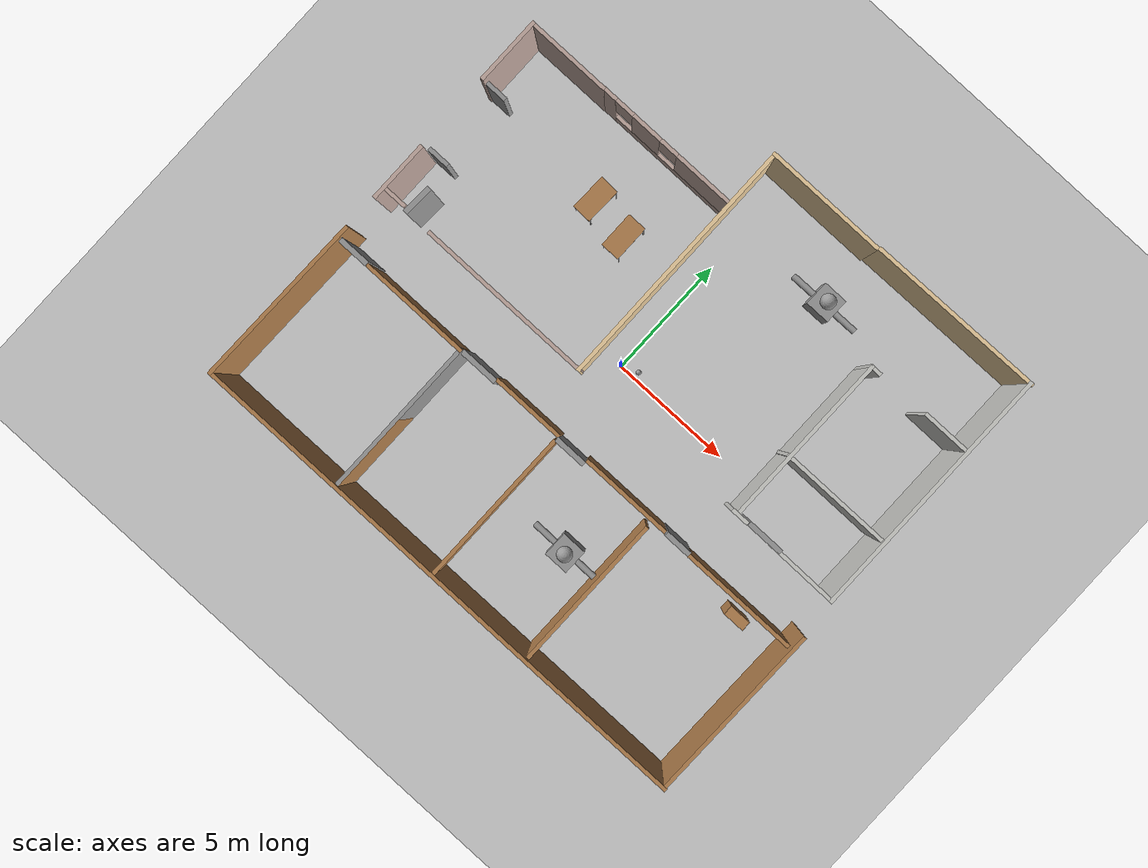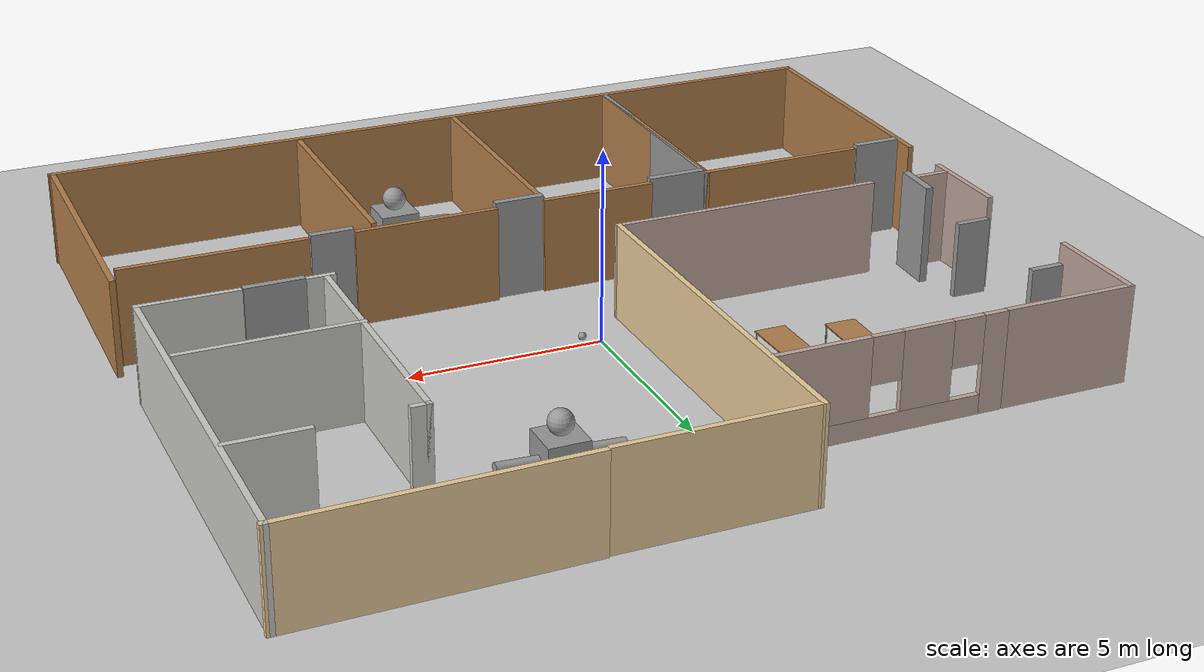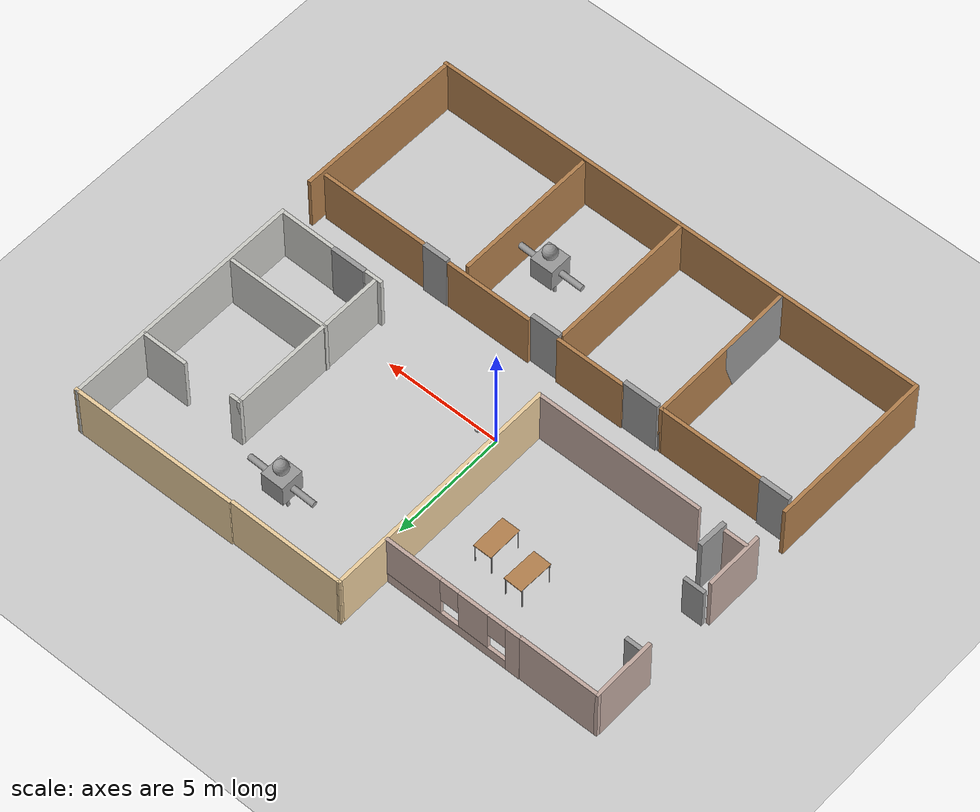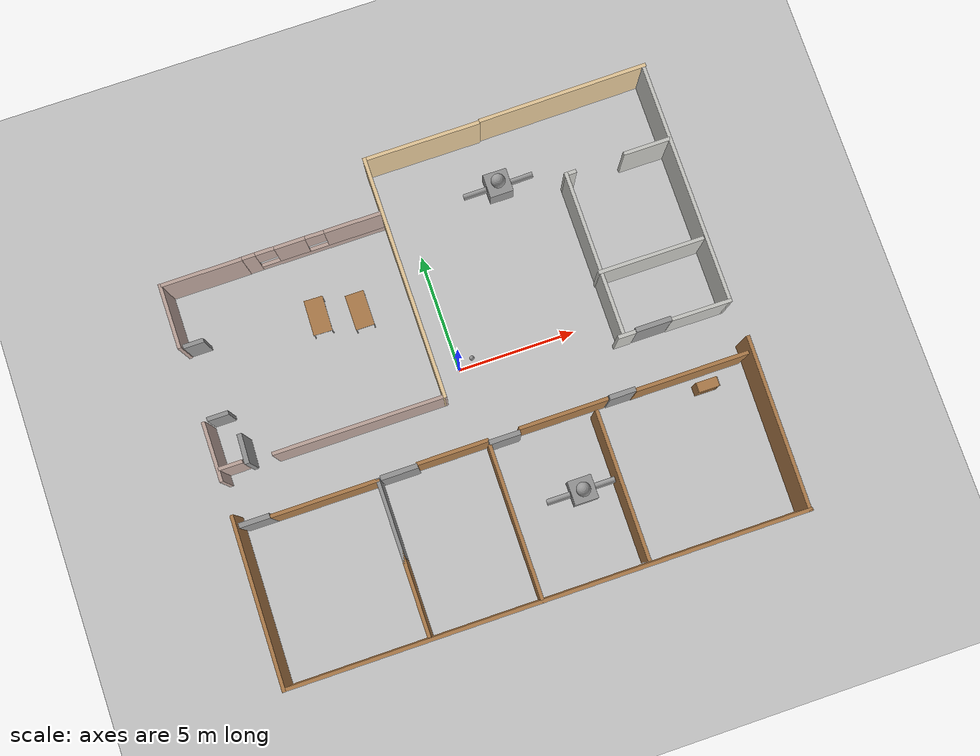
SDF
<sdf version="1.6">
 <world name="default">
  <plugin name="hello" filename="libhello.so"/>
  <light name="sun" type="directional">
   <pose>0 0 10 0 -0 0</pose>
   <diffuse>0.8 0.8 0.8 1</diffuse>
   <specular>0.2 0.2 0.2 1</specular>
   <attenuation>
    <range>1000</range>
    <constant>0.9</constant>
    <linear>0.01</linear>
    <quadratic>0.001</quadratic>
   </attenuation>
   <direction>-0.5 0.1 -0.9</direction>
  </light>
  <gravity>0 0 -9.8</gravity>
  <magnetic_field>6e-06 2.3e-05 -4.2e-05</magnetic_field>
  <atmosphere type="adiabatic"/>
  <physics name="default_physics" default="0" type="ode">
   <max_step_size>0.001</max_step_size>
   <real_time_factor>1</real_time_factor>
   <real_time_update_rate>1000</real_time_update_rate>
  </physics>
  <scene><ambient>0.4 0.4 0.4 1</ambient><background>0.7 0.7 0.7 1</background><shadows>1</shadows></scene>
  <spherical_coordinates>
   <surface_model>EARTH_WGS84</surface_model>
   <latitude_deg>0</latitude_deg>
   <longitude_deg>0</longitude_deg>
   <elevation>0</elevation>
   <heading_deg>0</heading_deg>
  </spherical_coordinates>
  <model name="Building">
   <pose>0.405506 -0.396401 0 0 -0 0</pose>
   <link name="Door_12">
    <collision name="Door_12_Collision">
     <geometry><box><size>1.264 0.2 2.6</size></box></geometry>
     <pose>0 0 1.3 0 -0 0</pose>
    </collision>
    <visual name="Door_12_Visual">
     <pose>0 0 1.3 0 -0 0</pose>
     <geometry><box><size>1.264 0.2 2.6</size></box></geometry>
     <material>
      <script><uri>file://media/materials/scripts/gazebo.material</uri><name>Gazebo/Grey</name></script>
     </material>
    </visual>
    <pose>-9.9622 -3.0454 0 0 -0 0</pose>
   </link>
   <link name="Door_13">
    <collision name="Door_13_Collision">
     <geometry><box><size>1.224 0.2 2.6</size></box></geometry>
     <pose>0 0 1.3 0 -0 0</pose>
    </collision>
    <visual name="Door_13_Visual">
     <pose>0 0 1.3 0 -0 0</pose>
     <geometry><box><size>1.224 0.2 2.6</size></box></geometry>
     <material>
      <script><uri>file://media/materials/scripts/gazebo.material</uri><name>Gazebo/Grey</name></script>
     </material>
    </visual>
    <pose>-9.53741 -0.213505 0 0 0 -1.61176</pose>
   </link>
   <link name="Door_14">
    <collision name="Door_14_Collision">
     <geometry><box><size>0.9 0.17 2</size></box></geometry>
     <pose>0 0 1 0 -0 0</pose>
    </collision>
    <visual name="Door_14_Visual">
     <pose>0 0 1 0 -0 0</pose>
     <geometry><box><size>0.9 0.17 2</size></box></geometry>
     <material>
      <script><uri>file://media/materials/scripts/gazebo.material</uri><name>Gazebo/Grey</name></script>
     </material>
    </visual>
    <pose>-10.2656 4.56025 0 0 -0 0</pose>
   </link>
   <link name="Door_15">
    <collision name="Door_15_Collision">
     <geometry><box><size>0.9 0.17 2</size></box></geometry>
     <pose>0 0 1 0 -0 0</pose>
    </collision>
    <visual name="Door_15_Visual">
     <pose>0 0 1 0 -0 0</pose>
     <geometry><box><size>0.9 0.17 2</size></box></geometry>
     <material>
      <script><uri>file://media/materials/scripts/gazebo.material</uri><name>Gazebo/Grey</name></script>
     </material>
    </visual>
    <pose>-10.1847 1.44517 0 0 -0 0</pose>
   </link>
   <link name="Door_16">
    <collision name="Door_16_Collision">
     <geometry><box><size>1.507 0.2 2.55</size></box></geometry>
     <pose>0 0 1.275 0 -0 0</pose>
    </collision>
    <visual name="Door_16_Visual">
     <pose>0 0 1.275 0 -0 0</pose>
     <geometry><box><size>1.507 0.2 2.55</size></box></geometry>
     <material>
      <script><uri>file://media/materials/scripts/gazebo.material</uri><name>Gazebo/Grey</name></script>
     </material>
    </visual>
    <pose>7.4337 -0.698972 0 0 -0 0</pose>
   </link>
   <link name="Door_5">
    <collision name="Door_5_Collision">
     <geometry><box><size>1.102 0.2 2.6</size></box></geometry>
     <pose>0 0 1.3 0 -0 0</pose>
    </collision>
    <visual name="Door_5_Visual">
     <pose>0 0 1.3 0 -0 0</pose>
     <geometry><box><size>1.102 0.2 2.6</size></box></geometry>
     <material>
      <script><uri>file://media/materials/scripts/gazebo.material</uri><name>Gazebo/Grey</name></script>
     </material>
    </visual>
    <pose>5.33001 -2.92403 0 0 -0 0</pose>
   </link>
   <link name="Door_6">
    <collision name="Door_6_Collision">
     <geometry><box><size>1.30456 0.2 2.6</size></box></geometry>
     <pose>0 0 1.3 0 -0 0</pose>
    </collision>
    <visual name="Door_6_Visual">
     <pose>0 0 1.3 0 -0 0</pose>
     <geometry><box><size>1.30456 0.2 2.6</size></box></geometry>
     <material>
      <script><uri>file://media/materials/scripts/gazebo.material</uri><name>Gazebo/Grey</name></script>
     </material>
    </visual>
    <pose>0.353974 -3.08585 0 0 -0 0</pose>
   </link>
   <link name="Door_7">
    <collision name="Door_7_Collision">
     <geometry><box><size>1.54729 0.2 2.6</size></box></geometry>
     <pose>0 0 1.3 0 -0 0</pose>
    </collision>
    <visual name="Door_7_Visual">
     <pose>0 0 1.3 0 -0 0</pose>
     <geometry><box><size>1.54729 0.2 2.6</size></box></geometry>
     <material>
      <script><uri>file://media/materials/scripts/gazebo.material</uri><name>Gazebo/Grey</name></script>
     </material>
    </visual>
    <pose>-4.01523 -3.0454 0 0 -0 0</pose>
   </link>
   <link name="Wall_100">
    <collision name="Wall_100_Collision">
     <geometry><box><size>7 0.15 2.5</size></box></geometry>
     <pose>0 0 1.25 0 -0 0</pose>
    </collision>
    <visual name="Wall_100_Visual">
     <pose>0 0 1.25 0 -0 0</pose>
     <geometry><box><size>7 0.15 2.5</size></box></geometry>
     <material>
      <script><uri>file://media/materials/scripts/gazebo.material</uri><name>Gazebo/CeilingTiled</name></script>
      <ambient>1 1 1 1</ambient>
     </material>
     <meta><layer>0</layer></meta>
    </visual>
    <pose>6.16803 2.83366 0 0 0 -1.5708</pose>
   </link>
   <link name="Wall_107">
    <collision name="Wall_107_Collision">
     <geometry><box><size>4.75 0.15 2.5</size></box></geometry>
     <pose>0 0 1.25 0 -0 0</pose>
    </collision>
    <visual name="Wall_107_Visual">
     <pose>0 0 1.25 0 -0 0</pose>
     <geometry><box><size>4.75 0.15 2.5</size></box></geometry>
     <material>
      <script><uri>file://media/materials/scripts/gazebo.material</uri><name>Gazebo/Wood</name></script>
      <ambient>0.603922 0.4 0.298039 1</ambient>
     </material>
     <meta><layer>0</layer></meta>
    </visual>
    <pose>8.26901 -2.96448 0 0 -0 3.14159</pose>
   </link>
   <link name="Wall_109">
    <collision name="Wall_109_Collision">
     <geometry><box><size>3.75 0.15 2.5</size></box></geometry>
     <pose>0 0 1.25 0 -0 0</pose>
    </collision>
    <visual name="Wall_109_Visual">
     <pose>0 0 1.25 0 -0 0</pose>
     <geometry><box><size>3.75 0.15 2.5</size></box></geometry>
     <material>
      <script><uri>file://media/materials/scripts/gazebo.material</uri><name>Gazebo/Wood</name></script>
      <ambient>0.603922 0.4 0.298039 1</ambient>
     </material>
     <meta><layer>0</layer></meta>
    </visual>
    <pose>2.86976 -2.92403 0 0 -0 3.14159</pose>
   </link>
   <link name="Wall_114">
    <collision name="Wall_114_Collision">
     <geometry><box><size>3 0.15 2.5</size></box></geometry>
     <pose>0 0 1.25 0 -0 0</pose>
    </collision>
    <visual name="Wall_114_Visual">
     <pose>0 0 1.25 0 -0 0</pose>
     <geometry><box><size>3 0.15 2.5</size></box></geometry>
     <material>
      <script><uri>file://media/materials/scripts/gazebo.material</uri><name>Gazebo/Wood</name></script>
      <ambient>0.603922 0.4 0.298039 1</ambient>
     </material>
     <meta><layer>0</layer></meta>
    </visual>
    <pose>-1.779 -2.96448 0 0 -0 3.14159</pose>
   </link>
   <link name="Wall_116">
    <collision name="Wall_116_Collision">
     <geometry><box><size>4.5 0.15 2.5</size></box></geometry>
     <pose>0 0 1.25 0 -0 0</pose>
    </collision>
    <visual name="Wall_116_Visual">
     <pose>0 0 1.25 0 -0 0</pose>
     <geometry><box><size>4.5 0.15 2.5</size></box></geometry>
     <material>
      <script><uri>file://media/materials/scripts/gazebo.material</uri><name>Gazebo/Wood</name></script>
      <ambient>0.603922 0.4 0.298039 1</ambient>
     </material>
     <meta><layer>0</layer></meta>
    </visual>
    <pose>-7.08148 -3.07404 0 0 -0 3.14159</pose>
   </link>
   <link name="Wall_51">
    <collision name="Wall_51_Collision">
     <geometry><box><size>7.12896 0.15 2.5</size></box></geometry>
     <pose>0 0 1.25 0 -0 0</pose>
    </collision>
    <visual name="Wall_51_Visual">
     <pose>0 0 1.25 0 -0 0</pose>
     <geometry><box><size>7.12896 0.15 2.5</size></box></geometry>
     <material>
      <script><uri>file://media/materials/scripts/gazebo.material</uri><name>Gazebo/Wood</name></script>
      <ambient>0.603922 0.4 0.298039 1</ambient>
     </material>
     <meta><layer>0</layer></meta>
    </visual>
    <pose>-10.8 -6.10067 0 0 0 -1.58239</pose>
   </link>
   <link name="Wall_52">
    <collision name="Wall_52_Collision">
     <geometry><box><size>21.75 0.15 2.5</size></box></geometry>
     <pose>0 0 1.25 0 -0 0</pose>
    </collision>
    <visual name="Wall_52_Visual">
     <pose>0 0 1.25 0 -0 0</pose>
     <geometry><box><size>21.75 0.15 2.5</size></box></geometry>
     <material>
      <script><uri>file://media/materials/scripts/gazebo.material</uri><name>Gazebo/Wood</name></script>
      <ambient>0.603922 0.4 0.298039 1</ambient>
     </material>
     <meta><layer>0</layer></meta>
    </visual>
    <pose>1.3e-05 -9.58992 0 0 -0 0</pose>
   </link>
   <link name="Wall_53">
    <collision name="Wall_53_Collision">
     <geometry><box><size>7.33863 0.15 2.5</size></box></geometry>
     <pose>0 0 1.25 0 -0 0</pose>
    </collision>
    <visual name="Wall_53_Visual">
     <pose>0 0 1.25 0 -0 0</pose>
     <geometry><box><size>7.33863 0.15 2.5</size></box></geometry>
     <material>
      <script><uri>file://media/materials/scripts/gazebo.material</uri><name>Gazebo/Wood</name></script>
      <ambient>0.603922 0.4 0.298039 1</ambient>
     </material>
     <meta><layer>0</layer></meta>
    </visual>
    <pose>10.8 -5.99583 0 0 -0 1.55954</pose>
   </link>
   <link name="Wall_68">
    <collision name="Wall_68_Collision">
     <geometry><box><size>6.5 0.15 2.5</size></box></geometry>
     <pose>0 0 1.25 0 -0 0</pose>
    </collision>
    <visual name="Wall_68_Visual">
     <pose>0 0 1.25 0 -0 0</pose>
     <geometry><box><size>6.5 0.15 2.5</size></box></geometry>
     <material>
      <script><uri>file://media/materials/scripts/gazebo.material</uri><name>Gazebo/Grey</name></script>
      <ambient>1 1 1 1</ambient>
     </material>
     <meta><layer>0</layer></meta>
    </visual>
    <pose>-4.90648 -6.24904 0 0 0 -1.5708</pose>
   </link>
   <link name="Wall_69">
    <collision name="Wall_69_Collision">
     <geometry><box><size>6.5 0.15 2.5</size></box></geometry>
     <pose>0 0 1.25 0 -0 0</pose>
    </collision>
    <visual name="Wall_69_Visual">
     <pose>0 0 1.25 0 -0 0</pose>
     <geometry><box><size>6.5 0.15 2.5</size></box></geometry>
     <material>
      <script><uri>file://media/materials/scripts/gazebo.material</uri><name>Gazebo/Wood</name></script>
      <ambient>0.603922 0.4 0.298039 1</ambient>
     </material>
     <meta><layer>0</layer></meta>
    </visual>
    <pose>-4.90648 -6.24904 0 0 -0 1.5708</pose>
   </link>
   <link name="Wall_71">
    <collision name="Wall_71_Collision">
     <geometry><box><size>6.5 0.15 2.5</size></box></geometry>
     <pose>0 0 1.25 0 -0 0</pose>
    </collision>
    <visual name="Wall_71_Visual">
     <pose>0 0 1.25 0 -0 0</pose>
     <geometry><box><size>6.5 0.15 2.5</size></box></geometry>
     <material>
      <script><uri>file://media/materials/scripts/gazebo.material</uri><name>Gazebo/Wood</name></script>
      <ambient>0.603922 0.4 0.298039 1</ambient>
     </material>
     <meta><layer>0</layer></meta>
    </visual>
    <pose>-0.300474 -6.39572 0 0 -0 1.5708</pose>
   </link>
   <link name="Wall_73">
    <collision name="Wall_73_Collision">
     <geometry><box><size>6.25 0.15 2.5</size></box></geometry>
     <pose>0 0 1.25 0 -0 0</pose>
    </collision>
    <visual name="Wall_73_Visual">
     <pose>0 0 1.25 0 -0 0</pose>
     <geometry><box><size>6.25 0.15 2.5</size></box></geometry>
     <material>
      <script><uri>file://media/materials/scripts/gazebo.material</uri><name>Gazebo/Wood</name></script>
      <ambient>0.603922 0.4 0.298039 1</ambient>
     </material>
     <meta><layer>0</layer></meta>
    </visual>
    <pose>4.14462 -6.3397 0 0 -0 1.5708</pose>
   </link>
   <link name="Wall_75">
    <collision name="Wall_75_Collision">
     <geometry><box><size>10.5 0.15 2.5</size></box></geometry>
     <pose>0 0 1.25 0 -0 0</pose>
    </collision>
    <visual name="Wall_75_Visual">
     <pose>0 0 1.25 0 -0 0</pose>
     <geometry><box><size>10.5 0.15 2.5</size></box></geometry>
     <material>
      <script><uri>file://media/materials/scripts/gazebo.material</uri><name>Gazebo/CeilingTiled</name></script>
      <ambient>1 1 1 1</ambient>
     </material>
     <meta><layer>0</layer></meta>
    </visual>
    <pose>10.6614 4.41494 0 0 -0 1.5708</pose>
   </link>
   <link name="Wall_76">
    <collision name="Wall_76_Collision">
     <geometry><box><size>7.24417 0.15 2.5</size></box></geometry>
     <pose>0 0 1.25 0 -0 0</pose>
    </collision>
    <visual name="Wall_76_Visual">
     <pose>0 0 1.25 0 -0 0</pose>
     <geometry><box><size>7.24417 0.15 2.5</size></box></geometry>
     <material>
      <script><uri>file://media/materials/scripts/gazebo.material</uri><name>Gazebo/Grey</name></script>
      <ambient>0.921569 0.807843 0.615686 1</ambient>
     </material>
     <meta><layer>0</layer></meta>
    </visual>
    <pose>7.15502 9.54948 0 0 0 -3.13019</pose>
   </link>
   <link name="Wall_78">
    <collision name="Wall_78_Collision">
     <geometry><box><size>5 0.15 2.5</size></box></geometry>
     <pose>0 0 1.25 0 -0 0</pose>
    </collision>
    <visual name="Wall_78_Visual">
     <pose>0 0 1.25 0 -0 0</pose>
     <geometry><box><size>5 0.15 2.5</size></box></geometry>
     <material>
      <script><uri>file://media/materials/scripts/gazebo.material</uri><name>Gazebo/Grey</name></script>
      <ambient>0.921569 0.807843 0.615686 1</ambient>
     </material>
     <meta><layer>0</layer></meta>
    </visual>
    <pose>1.03576 9.45672 0 0 -0 3.14159</pose>
   </link>
   <link name="Wall_79">
    <collision name="Wall_79_Collision">
     <geometry><box><size>10.3677 0.15 2.5</size></box></geometry>
     <pose>0 0 1.25 0 -0 0</pose>
    </collision>
    <visual name="Wall_79_Visual">
     <pose>0 0 1.25 0 -0 0</pose>
     <geometry><box><size>10.3677 0.15 2.5</size></box></geometry>
     <material>
      <script><uri>file://media/materials/scripts/gazebo.material</uri><name>Gazebo/Grey</name></script>
      <ambient>0.921569 0.807843 0.615686 1</ambient>
     </material>
     <meta><layer>0</layer></meta>
    </visual>
    <pose>-1.37786 4.34787 0 0 0 -1.56857</pose>
   </link>
   <link name="Wall_80">
    <collision name="Wall_80_Collision">
     <geometry><box><size>7.25 0.15 2.5</size></box></geometry>
     <pose>0 0 1.25 0 -0 0</pose>
    </collision>
    <visual name="Wall_80_Visual">
     <pose>0 0 1.25 0 -0 0</pose>
     <geometry><box><size>7.25 0.15 2.5</size></box></geometry>
     <material>
      <script><uri>file://media/materials/scripts/gazebo.material</uri><name>Gazebo/Grey</name></script>
      <ambient>0.760784 0.662745 0.627451 1</ambient>
     </material>
     <meta><layer>0</layer></meta>
    </visual>
    <pose>-4.91649 -0.760978 0 0 -0 3.14159</pose>
   </link>
   <link name="Wall_82">
    <collision name="Wall_82_Collision">
     <geometry><box><size>1 0.15 2.5</size></box></geometry>
     <pose>0 0 1.25 0 -0 0</pose>
    </collision>
    <visual name="Wall_82_Visual">
     <pose>0 0 1.25 0 -0 0</pose>
     <geometry><box><size>1 0.15 2.5</size></box></geometry>
     <material>
      <script><uri>file://media/materials/scripts/gazebo.material</uri><name>Gazebo/Grey</name></script>
      <ambient>0.760784 0.662745 0.627451 1</ambient>
     </material>
     <meta><layer>0</layer></meta>
    </visual>
    <pose>-10.2186 -0.659725 0 0 -0 3.14159</pose>
   </link>
   <link name="Wall_84">
    <collision name="Wall_84_Collision">
     <geometry><box><size>2.5 0.15 2.5</size></box></geometry>
     <pose>0 0 1.25 0 -0 0</pose>
    </collision>
    <visual name="Wall_84_Visual">
     <pose>0 0 1.25 0 -0 0</pose>
     <geometry><box><size>2.5 0.15 2.5</size></box></geometry>
     <material>
      <script><uri>file://media/materials/scripts/gazebo.material</uri><name>Gazebo/Grey</name></script>
      <ambient>0.760784 0.662745 0.627451 1</ambient>
     </material>
     <meta><layer>0</layer></meta>
    </visual>
    <pose>-10.7394 0.072092 0 0 -0 1.5708</pose>
   </link>
   <link name="Wall_86">
    <collision name="Wall_86_Collision">
     <geometry><box><size>2.75 0.15 2.5</size></box></geometry>
     <pose>0 0 1.25 0 -0 0</pose>
    </collision>
    <visual name="Wall_86_Visual">
     <pose>0 0 1.25 0 -0 0</pose>
     <geometry><box><size>2.75 0.15 2.5</size></box></geometry>
     <material>
      <script><uri>file://media/materials/scripts/gazebo.material</uri><name>Gazebo/Grey</name></script>
      <ambient>0.760784 0.662745 0.627451 1</ambient>
     </material>
     <meta><layer>0</layer></meta>
    </visual>
    <pose>-10.7595 5.80878 0 0 -0 1.5708</pose>
   </link>
   <link name="Wall_87">
    <collision name="Wall_87_Collision">
     <geometry><box><size>3.5 0.15 2.5</size></box></geometry>
     <pose>0 0 1.25 0 -0 0</pose>
    </collision>
    <visual name="Wall_87_Visual">
     <pose>0 0 1.25 0 -0 0</pose>
     <geometry><box><size>3.5 0.15 2.5</size></box></geometry>
     <material>
      <script><uri>file://media/materials/scripts/gazebo.material</uri><name>Gazebo/Grey</name></script>
      <ambient>0.760784 0.662745 0.627451 1</ambient>
     </material>
     <meta><layer>0</layer></meta>
    </visual>
    <pose>-9.08453 7.10878 0 0 -0 0</pose>
   </link>
   <link name="Wall_89">
    <pose>-4.39819 7.12354 0 0 -0 0</pose>
    <visual name="Wall_89_Visual_0">
     <pose>-2.69184 0 1.25 0 -0 0</pose>
     <geometry><box><size>0.61631 0.15 2.5</size></box></geometry>
     <material>
      <script><uri>file://media/materials/scripts/gazebo.material</uri><name>Gazebo/Grey</name></script>
      <ambient>0.760784 0.662745 0.627451 1</ambient>
     </material>
     <meta><layer>0</layer></meta>
    </visual>
    <collision name="Wall_89_Collision_0">
     <geometry><box><size>0.61631 0.15 2.5</size></box></geometry>
     <pose>-2.69184 0 1.25 0 -0 0</pose>
    </collision>
    <visual name="Wall_89_Visual_1">
     <pose>0.308155 0 0.25 0 -0 0</pose>
     <geometry><box><size>5.38369 0.15 0.5</size></box></geometry>
     <material>
      <script><uri>file://media/materials/scripts/gazebo.material</uri><name>Gazebo/Grey</name></script>
      <ambient>0.760784 0.662745 0.627451 1</ambient>
     </material>
     <meta><layer>0</layer></meta>
    </visual>
    <collision name="Wall_89_Collision_1">
     <geometry><box><size>5.38369 0.15 0.5</size></box></geometry>
     <pose>0.308155 0 0.25 0 -0 0</pose>
    </collision>
    <visual name="Wall_89_Visual_2">
     <pose>-0.931845 0 1.5 0 -0 0</pose>
     <geometry><box><size>1.30369 0.15 2</size></box></geometry>
     <material>
      <script><uri>file://media/materials/scripts/gazebo.material</uri><name>Gazebo/Grey</name></script>
      <ambient>0.760784 0.662745 0.627451 1</ambient>
     </material>
     <meta><layer>0</layer></meta>
    </visual>
    <collision name="Wall_89_Collision_2">
     <geometry><box><size>1.30369 0.15 2</size></box></geometry>
     <pose>-0.931845 0 1.5 0 -0 0</pose>
    </collision>
    <visual name="Wall_89_Visual_3">
     <pose>1.76 0 1.5 0 -0 0</pose>
     <geometry><box><size>2.48 0.15 2</size></box></geometry>
     <material>
      <script><uri>file://media/materials/scripts/gazebo.material</uri><name>Gazebo/Grey</name></script>
      <ambient>0.760784 0.662745 0.627451 1</ambient>
     </material>
     <meta><layer>0</layer></meta>
    </visual>
    <collision name="Wall_89_Collision_3">
     <geometry><box><size>2.48 0.15 2</size></box></geometry>
     <pose>1.76 0 1.5 0 -0 0</pose>
    </collision>
    <visual name="Wall_89_Visual_4">
     <pose>-1.98369 0 1.9 0 -0 0</pose>
     <geometry><box><size>0.8 0.15 1.2</size></box></geometry>
     <material>
      <script><uri>file://media/materials/scripts/gazebo.material</uri><name>Gazebo/Grey</name></script>
      <ambient>0.760784 0.662745 0.627451 1</ambient>
     </material>
     <meta><layer>0</layer></meta>
    </visual>
    <collision name="Wall_89_Collision_4">
     <geometry><box><size>0.8 0.15 1.2</size></box></geometry>
     <pose>-1.98369 0 1.9 0 -0 0</pose>
    </collision>
    <visual name="Wall_89_Visual_5">
     <pose>0.119999 0 1.9 0 -0 0</pose>
     <geometry><box><size>0.8 0.15 1.2</size></box></geometry>
     <material>
      <script><uri>file://media/materials/scripts/gazebo.material</uri><name>Gazebo/Grey</name></script>
      <ambient>0.760784 0.662745 0.627451 1</ambient>
     </material>
     <meta><layer>0</layer></meta>
    </visual>
    <collision name="Wall_89_Collision_5">
     <geometry><box><size>0.8 0.15 1.2</size></box></geometry>
     <pose>0.119999 0 1.9 0 -0 0</pose>
    </collision>
   </link>
   <link name="Wall_91">
    <collision name="Wall_91_Collision">
     <geometry><box><size>2 0.15 2.5</size></box></geometry>
     <pose>0 0 1.25 0 -0 0</pose>
    </collision>
    <visual name="Wall_91_Visual">
     <pose>0 0 1.25 0 -0 0</pose>
     <geometry><box><size>2 0.15 2.5</size></box></geometry>
     <material>
      <script><uri>file://media/materials/scripts/gazebo.material</uri><name>Gazebo/CeilingTiled</name></script>
      <ambient>1 1 1 1</ambient>
     </material>
     <meta><layer>0</layer></meta>
    </visual>
    <pose>9.65597 6.319 0 0 -0 3.14159</pose>
   </link>
   <link name="Wall_93">
    <collision name="Wall_93_Collision">
     <geometry><box><size>4.5 0.15 2.5</size></box></geometry>
     <pose>0 0 1.25 0 -0 0</pose>
    </collision>
    <visual name="Wall_93_Visual">
     <pose>0 0 1.25 0 -0 0</pose>
     <geometry><box><size>4.5 0.15 2.5</size></box></geometry>
     <material>
      <script><uri>file://media/materials/scripts/gazebo.material</uri><name>Gazebo/CeilingTiled</name></script>
      <ambient>1 1 1 1</ambient>
     </material>
     <meta><layer>0</layer></meta>
    </visual>
    <pose>8.3054 1.99458 0 0 -0 3.14159</pose>
   </link>
   <link name="Wall_95">
    <collision name="Wall_95_Collision">
     <geometry><box><size>2.56042 0.15 2.5</size></box></geometry>
     <pose>0 0 1.25 0 -0 0</pose>
    </collision>
    <visual name="Wall_95_Visual">
     <pose>0 0 1.25 0 -0 0</pose>
     <geometry><box><size>2.56042 0.15 2.5</size></box></geometry>
     <material>
      <script><uri>file://media/materials/scripts/gazebo.material</uri><name>Gazebo/CeilingTiled</name></script>
      <ambient>1 1 1 1</ambient>
     </material>
     <meta><layer>0</layer></meta>
    </visual>
    <pose>9.45625 -0.750464 0 0 -0 3.13363</pose>
   </link>
   <link name="Wall_97">
    <collision name="Wall_97_Collision">
     <geometry><box><size>0.75 0.15 2.5</size></box></geometry>
     <pose>0 0 1.25 0 -0 0</pose>
    </collision>
    <visual name="Wall_97_Visual">
     <pose>0 0 1.25 0 -0 0</pose>
     <geometry><box><size>0.75 0.15 2.5</size></box></geometry>
     <material>
      <script><uri>file://media/materials/scripts/gazebo.material</uri><name>Gazebo/CeilingTiled</name></script>
      <ambient>1 1 1 1</ambient>
     </material>
     <meta><layer>0</layer></meta>
    </visual>
    <pose>6.29848 -0.740864 0 0 -0 3.14159</pose>
   </link>
   <link name="Wall_99">
    <collision name="Wall_99_Collision">
     <geometry><box><size>0.5 0.15 2.5</size></box></geometry>
     <pose>0 0 1.25 0 -0 0</pose>
    </collision>
    <visual name="Wall_99_Visual">
     <pose>0 0 1.25 0 -0 0</pose>
     <geometry><box><size>0.5 0.15 2.5</size></box></geometry>
     <material>
      <script><uri>file://media/materials/scripts/gazebo.material</uri><name>Gazebo/CeilingTiled</name></script>
      <ambient>1 1 1 1</ambient>
     </material>
     <meta><layer>0</layer></meta>
    </visual>
    <pose>6.34303 6.25866 0 0 -0 3.14159</pose>
   </link>
   <static>1</static>
  </model>
  <model name="bookshelf">
   <static>1</static>
   <link name="link">
    <inertial><mass>1</mass></inertial>
    <collision name="back">
     <pose>0 0.005 0.6 0 -0 0</pose>
     <geometry><box><size>0.9 0.01 1.2</size></box></geometry>
    </collision>
    <visual name="visual1">
     <pose>0 0.005 0.6 0 -0 0</pose>
     <geometry><box><size>0.9 0.01 1.2</size></box></geometry>
     <material>
      <script><uri>file://media/materials/scripts/gazebo.material</uri><name>Gazebo/Wood</name></script>
     </material>
    </visual>
    <collision name="left_side">
     <pose>0.45 -0.195 0.6 0 -0 0</pose>
     <geometry><box><size>0.02 0.4 1.2</size></box></geometry>
    </collision>
    <visual name="visual2">
     <pose>0.45 -0.195 0.6 0 -0 0</pose>
     <geometry><box><size>0.02 0.4 1.2</size></box></geometry>
     <material>
      <script><uri>file://media/materials/scripts/gazebo.material</uri><name>Gazebo/Wood</name></script>
     </material>
    </visual>
    <collision name="right_side">
     <pose>-0.45 -0.195 0.6 0 -0 0</pose>
     <geometry><box><size>0.02 0.4 1.2</size></box></geometry>
    </collision>
    <visual name="visual3">
     <pose>-0.45 -0.195 0.6 0 -0 0</pose>
     <geometry><box><size>0.02 0.4 1.2</size></box></geometry>
     <material>
      <script><uri>file://media/materials/scripts/gazebo.material</uri><name>Gazebo/Wood</name></script>
     </material>
    </visual>
    <collision name="bottom">
     <pose>0 -0.195 0.03 0 -0 0</pose>
     <geometry><box><size>0.88 0.4 0.06</size></box></geometry>
    </collision>
    <visual name="visual4">
     <pose>0 -0.195 0.03 0 -0 0</pose>
     <geometry><box><size>0.88 0.4 0.06</size></box></geometry>
     <material>
      <script><uri>file://media/materials/scripts/gazebo.material</uri><name>Gazebo/Wood</name></script>
     </material>
    </visual>
    <collision name="top">
     <pose>0 -0.195 1.19 0 -0 0</pose>
     <geometry><box><size>0.88 0.4 0.02</size></box></geometry>
    </collision>
    <visual name="visual5">
     <pose>0 -0.195 1.19 0 -0 0</pose>
     <geometry><box><size>0.88 0.4 0.02</size></box></geometry>
     <material>
      <script><uri>file://media/materials/scripts/gazebo.material</uri><name>Gazebo/Wood</name></script>
     </material>
    </visual>
    <collision name="low_shelf">
     <pose>0 -0.195 0.43 0 -0 0</pose>
     <geometry><box><size>0.88 0.4 0.02</size></box></geometry>
    </collision>
    <visual name="visual6">
     <pose>0 -0.195 0.43 0 -0 0</pose>
     <geometry><box><size>0.88 0.4 0.02</size></box></geometry>
     <material>
      <script><uri>file://media/materials/scripts/gazebo.material</uri><name>Gazebo/Wood</name></script>
     </material>
    </visual>
    <collision name="high_shelf">
     <pose>0 -0.195 0.8 0 -0 0</pose>
     <geometry><box><size>0.88 0.4 0.02</size></box></geometry>
    </collision>
    <visual name="visual7">
     <pose>0 -0.195 0.8 0 -0 0</pose>
     <geometry><box><size>0.88 0.4 0.02</size></box></geometry>
     <material>
      <script><uri>file://media/materials/scripts/gazebo.material</uri><name>Gazebo/Wood</name></script>
     </material>
    </visual>
   </link>
   <pose>9.31281 -3.75165 0 0 -0 0</pose>
  </model>
  <model name="table">
   <static>1</static>
   <link name="link">
    <collision name="surface">
     <pose>0 0 1 0 -0 0</pose>
     <geometry><box><size>1.5 0.8 0.03</size></box></geometry>
     <surface><friction><ode><mu>0.6</mu><mu2>0.6</mu2></ode></friction></surface>
    </collision>
    <visual name="visual1">
     <pose>0 0 1 0 -0 0</pose>
     <geometry><box><size>1.5 0.8 0.03</size></box></geometry>
     <material>
      <script><uri>file://media/materials/scripts/gazebo.material</uri><name>Gazebo/Wood</name></script>
     </material>
    </visual>
    <collision name="front_left_leg">
     <pose>0.68 0.38 0.5 0 -0 0</pose>
     <geometry><cylinder><radius>0.02</radius><length>1</length></cylinder></geometry>
    </collision>
    <visual name="front_left_leg">
     <pose>0.68 0.38 0.5 0 -0 0</pose>
     <geometry><cylinder><radius>0.02</radius><length>1</length></cylinder></geometry>
     <material>
      <script><uri>file://media/materials/scripts/gazebo.material</uri><name>Gazebo/Grey</name></script>
     </material>
    </visual>
    <collision name="front_right_leg">
     <pose>0.68 -0.38 0.5 0 -0 0</pose>
     <geometry><cylinder><radius>0.02</radius><length>1</length></cylinder></geometry>
    </collision>
    <visual name="front_right_leg">
     <pose>0.68 -0.38 0.5 0 -0 0</pose>
     <geometry><cylinder><radius>0.02</radius><length>1</length></cylinder></geometry>
     <material>
      <script><uri>file://media/materials/scripts/gazebo.material</uri><name>Gazebo/Grey</name></script>
     </material>
    </visual>
    <collision name="back_right_leg">
     <pose>-0.68 -0.38 0.5 0 -0 0</pose>
     <geometry><cylinder><radius>0.02</radius><length>1</length></cylinder></geometry>
    </collision>
    <visual name="back_right_leg">
     <pose>-0.68 -0.38 0.5 0 -0 0</pose>
     <geometry><cylinder><radius>0.02</radius><length>1</length></cylinder></geometry>
     <material>
      <script><uri>file://media/materials/scripts/gazebo.material</uri><name>Gazebo/Grey</name></script>
     </material>
    </visual>
    <collision name="back_left_leg">
     <pose>-0.68 0.38 0.5 0 -0 0</pose>
     <geometry><cylinder><radius>0.02</radius><length>1</length></cylinder></geometry>
    </collision>
    <visual name="back_left_leg">
     <pose>-0.68 0.38 0.5 0 -0 0</pose>
     <geometry><cylinder><radius>0.02</radius><length>1</length></cylinder></geometry>
     <material>
      <script><uri>file://media/materials/scripts/gazebo.material</uri><name>Gazebo/Grey</name></script>
     </material>
    </visual>
   </link>
   <pose>-3.11227 3.51929 0 0 0 -1.5691</pose>
  </model>
  <model name="table_clone">
   <static>1</static>
   <link name="link">
    <collision name="surface">
     <pose>0 0 1 0 -0 0</pose>
     <geometry><box><size>1.5 0.8 0.03</size></box></geometry>
     <surface><friction><ode><mu>0.6</mu><mu2>0.6</mu2></ode></friction></surface>
    </collision>
    <visual name="visual1">
     <pose>0 0 1 0 -0 0</pose>
     <geometry><box><size>1.5 0.8 0.03</size></box></geometry>
     <material>
      <script><uri>file://media/materials/scripts/gazebo.material</uri><name>Gazebo/Wood</name></script>
     </material>
    </visual>
    <collision name="front_left_leg">
     <pose>0.68 0.38 0.5 0 -0 0</pose>
     <geometry><cylinder><radius>0.02</radius><length>1</length></cylinder></geometry>
    </collision>
    <visual name="front_left_leg">
     <pose>0.68 0.38 0.5 0 -0 0</pose>
     <geometry><cylinder><radius>0.02</radius><length>1</length></cylinder></geometry>
     <material>
      <script><uri>file://media/materials/scripts/gazebo.material</uri><name>Gazebo/Grey</name></script>
     </material>
    </visual>
    <collision name="front_right_leg">
     <pose>0.68 -0.38 0.5 0 -0 0</pose>
     <geometry><cylinder><radius>0.02</radius><length>1</length></cylinder></geometry>
    </collision>
    <visual name="front_right_leg">
     <pose>0.68 -0.38 0.5 0 -0 0</pose>
     <geometry><cylinder><radius>0.02</radius><length>1</length></cylinder></geometry>
     <material>
      <script><uri>file://media/materials/scripts/gazebo.material</uri><name>Gazebo/Grey</name></script>
     </material>
    </visual>
    <collision name="back_right_leg">
     <pose>-0.68 -0.38 0.5 0 -0 0</pose>
     <geometry><cylinder><radius>0.02</radius><length>1</length></cylinder></geometry>
    </collision>
    <visual name="back_right_leg">
     <pose>-0.68 -0.38 0.5 0 -0 0</pose>
     <geometry><cylinder><radius>0.02</radius><length>1</length></cylinder></geometry>
     <material>
      <script><uri>file://media/materials/scripts/gazebo.material</uri><name>Gazebo/Grey</name></script>
     </material>
    </visual>
    <collision name="back_left_leg">
     <pose>-0.68 0.38 0.5 0 -0 0</pose>
     <geometry><cylinder><radius>0.02</radius><length>1</length></cylinder></geometry>
    </collision>
    <visual name="back_left_leg">
     <pose>-0.68 0.38 0.5 0 -0 0</pose>
     <geometry><cylinder><radius>0.02</radius><length>1</length></cylinder></geometry>
     <material>
      <script><uri>file://media/materials/scripts/gazebo.material</uri><name>Gazebo/Grey</name></script>
     </material>
    </visual>
   </link>
   <pose>-4.79599 3.84583 0 0 0 -1.59841</pose>
  </model>
  <model name="ground_plane">
   <static>1</static>
   <link name="link">
    <collision name="collision">
     <geometry><plane><normal>0 0 1</normal><size>100 100</size></plane></geometry>
     <surface><friction><ode><mu>100</mu><mu2>50</mu2></ode></friction></surface>
    </collision>
    <visual name="visual">
     <cast_shadows>0</cast_shadows>
     <geometry><plane><normal>0 0 1</normal><size>100 100</size></plane></geometry>
     <material>
      <script><uri>file://media/materials/scripts/gazebo.material</uri><name>Gazebo/Grey</name></script>
     </material>
    </visual>
   </link>
   <pose>-3.8747 13.4824 0 0 -0 0</pose>
  </model>
  <light name="user_point_light_0" type="point">
   <pose>-1.87393 -12.1483 1 0 -0 0</pose>
   <diffuse>0.5 0.5 0.5 1</diffuse>
   <specular>0.1 0.1 0.1 1</specular>
   <attenuation>
    <range>20</range>
    <constant>0.5</constant>
    <linear>0.01</linear>
    <quadratic>0.001</quadratic>
   </attenuation>
   <cast_shadows>0</cast_shadows>
   <direction>0 0 -1</direction>
  </light>
  <model name="first_model-edited">
   <link name="link_0">
    <pose>1.34948 -1.03796 -0.376734 0 -0 0</pose>
    <inertial>
     <mass>0.0094372</mass>
     <inertia>
      <ixx>0.00013078</ixx>
      <ixy>0</ixy>
      <ixz>0</ixz>
      <iyy>6.914e-05</iyy>
      <iyz>0</iyz>
      <izz>0.00018908</izz>
     </inertia>
    </inertial>
    <visual name="visual">
     <geometry><box><size>0.284636 0.399254 0.083044</size></box></geometry>
     <material>
      <lighting>1</lighting>
      <script><uri>file://media/materials/scripts/gazebo.material</uri><name>Gazebo/Grey</name></script>
      <shader type="pixel"><normal_map>__default__</normal_map></shader>
      <ambient>0.3 0.3 0.3 1</ambient>
      <diffuse>0.7 0.7 0.7 1</diffuse>
      <specular>0.01 0.01 0.01 1</specular>
      <emissive>0 0 0 1</emissive>
     </material>
    </visual>
    <collision name="collision">
     <geometry><box><size>0.284636 0.399254 0.083044</size></box></geometry>
     <surface>
      <friction>
       <ode><mu>1</mu><mu2>1</mu2><fdir1>0 0 0</fdir1><slip1>0</slip1><slip2>0</slip2></ode>
       <torsional>
        <coefficient>1</coefficient>
        <patch_radius>0</patch_radius>
        <surface_radius>0</surface_radius>
        <use_patch_radius>1</use_patch_radius>
        <ode><slip>0</slip></ode>
       </torsional>
      </friction>
      <bounce><restitution_coefficient>0</restitution_coefficient><threshold>1e+06</threshold></bounce>
      <contact>
       <collide_without_contact>0</collide_without_contact>
       <collide_without_contact_bitmask>1</collide_without_contact_bitmask>
       <collide_bitmask>1</collide_bitmask>
       <ode>
        <soft_cfm>0</soft_cfm>
        <soft_erp>0.2</soft_erp>
        <kp>1e+13</kp>
        <kd>1</kd>
        <max_vel>0.01</max_vel>
        <min_depth>0</min_depth>
       </ode>
       <bullet>
        <split_impulse>1</split_impulse>
        <split_impulse_penetration_threshold>-0.01</split_impulse_penetration_threshold>
        <soft_cfm>0</soft_cfm>
        <soft_erp>0.2</soft_erp>
        <kp>1e+13</kp>
        <kd>1</kd>
       </bullet>
      </contact>
     </surface>
    </collision>
   </link>
   <link name="link_0_clone">
    <pose>0.761524 -0.928795 -0.376734 0 -0 0</pose>
    <inertial>
     <mass>0.0094372</mass>
     <inertia>
      <ixx>0.00013078</ixx>
      <ixy>0</ixy>
      <ixz>0</ixz>
      <iyy>6.914e-05</iyy>
      <iyz>0</iyz>
      <izz>0.00018908</izz>
     </inertia>
    </inertial>
    <visual name="visual">
     <geometry><box><size>0.284636 0.399254 0.083044</size></box></geometry>
     <material>
      <lighting>1</lighting>
      <script><uri>file://media/materials/scripts/gazebo.material</uri><name>Gazebo/Grey</name></script>
      <shader type="pixel"><normal_map>__default__</normal_map></shader>
      <ambient>0.3 0.3 0.3 1</ambient>
      <diffuse>0.7 0.7 0.7 1</diffuse>
      <specular>0.01 0.01 0.01 1</specular>
      <emissive>0 0 0 1</emissive>
     </material>
    </visual>
    <collision name="collision">
     <geometry><box><size>0.284636 0.399254 0.083044</size></box></geometry>
     <surface>
      <friction>
       <ode><mu>1</mu><mu2>1</mu2><fdir1>0 0 0</fdir1><slip1>0</slip1><slip2>0</slip2></ode>
       <torsional>
        <coefficient>1</coefficient>
        <patch_radius>0</patch_radius>
        <surface_radius>0</surface_radius>
        <use_patch_radius>1</use_patch_radius>
        <ode><slip>0</slip></ode>
       </torsional>
      </friction>
      <bounce><restitution_coefficient>0</restitution_coefficient><threshold>1e+06</threshold></bounce>
      <contact>
       <collide_without_contact>0</collide_without_contact>
       <collide_without_contact_bitmask>1</collide_without_contact_bitmask>
       <collide_bitmask>1</collide_bitmask>
       <ode>
        <soft_cfm>0</soft_cfm>
        <soft_erp>0.2</soft_erp>
        <kp>1e+13</kp>
        <kd>1</kd>
        <max_vel>0.01</max_vel>
        <min_depth>0</min_depth>
       </ode>
       <bullet>
        <split_impulse>1</split_impulse>
        <split_impulse_penetration_threshold>-0.01</split_impulse_penetration_threshold>
        <soft_cfm>0</soft_cfm>
        <soft_erp>0.2</soft_erp>
        <kp>1e+13</kp>
        <kd>1</kd>
       </bullet>
      </contact>
     </surface>
    </collision>
   </link>
   <link name="link_1">
    <pose>0.763842 -0.869168 0.081744 0 -0 0</pose>
    <inertial>
     <mass>0.0171814</mass>
     <inertia>
      <ixx>0.00145024</ixx>
      <ixy>0</ixy>
      <ixz>0</ixz>
      <iyy>0.00145024</iyy>
      <iyz>0</iyz>
      <izz>3.69e-05</izz>
     </inertia>
    </inertial>
    <visual name="visual">
     <geometry><cylinder><radius>0.0655402</radius><length>1</length></cylinder></geometry>
     <material>
      <lighting>1</lighting>
      <script><uri>file://media/materials/scripts/gazebo.material</uri><name>Gazebo/Grey</name></script>
      <shader type="pixel"><normal_map>__default__</normal_map></shader>
      <ambient>0.3 0.3 0.3 1</ambient>
      <diffuse>0.7 0.7 0.7 1</diffuse>
      <specular>0.01 0.01 0.01 1</specular>
      <emissive>0 0 0 1</emissive>
     </material>
    </visual>
    <collision name="collision">
     <geometry><cylinder><radius>0.06554</radius><length>1</length></cylinder></geometry>
     <surface>
      <friction>
       <ode><mu>1</mu><mu2>1</mu2><fdir1>0 0 0</fdir1><slip1>0</slip1><slip2>0</slip2></ode>
       <torsional>
        <coefficient>1</coefficient>
        <patch_radius>0</patch_radius>
        <surface_radius>0</surface_radius>
        <use_patch_radius>1</use_patch_radius>
        <ode><slip>0</slip></ode>
       </torsional>
      </friction>
      <bounce><restitution_coefficient>0</restitution_coefficient><threshold>1e+06</threshold></bounce>
      <contact>
       <collide_without_contact>0</collide_without_contact>
       <collide_without_contact_bitmask>1</collide_without_contact_bitmask>
       <collide_bitmask>1</collide_bitmask>
       <ode>
        <soft_cfm>0</soft_cfm>
        <soft_erp>0.2</soft_erp>
        <kp>1e+13</kp>
        <kd>1</kd>
        <max_vel>0.01</max_vel>
        <min_depth>0</min_depth>
       </ode>
       <bullet>
        <split_impulse>1</split_impulse>
        <split_impulse_penetration_threshold>-0.01</split_impulse_penetration_threshold>
        <soft_cfm>0</soft_cfm>
        <soft_erp>0.2</soft_erp>
        <kp>1e+13</kp>
        <kd>1</kd>
       </bullet>
      </contact>
     </surface>
    </collision>
   </link>
   <link name="link_1_clone">
    <pose>1.34948 -0.903875 0.081744 0 -0 0</pose>
    <inertial>
     <mass>0.0171814</mass>
     <inertia>
      <ixx>0.00145024</ixx>
      <ixy>0</ixy>
      <ixz>0</ixz>
      <iyy>0.00145024</iyy>
      <iyz>0</iyz>
      <izz>3.69e-05</izz>
     </inertia>
    </inertial>
    <visual name="visual">
     <geometry><cylinder><radius>0.0655402</radius><length>1</length></cylinder></geometry>
     <material>
      <lighting>1</lighting>
      <script><uri>file://media/materials/scripts/gazebo.material</uri><name>Gazebo/Grey</name></script>
      <shader type="pixel"><normal_map>__default__</normal_map></shader>
      <ambient>0.3 0.3 0.3 1</ambient>
      <diffuse>0.7 0.7 0.7 1</diffuse>
      <specular>0.01 0.01 0.01 1</specular>
      <emissive>0 0 0 1</emissive>
     </material>
    </visual>
    <collision name="collision">
     <geometry><cylinder><radius>0.06554</radius><length>1</length></cylinder></geometry>
     <surface>
      <friction>
       <ode><mu>1</mu><mu2>1</mu2><fdir1>0 0 0</fdir1><slip1>0</slip1><slip2>0</slip2></ode>
       <torsional>
        <coefficient>1</coefficient>
        <patch_radius>0</patch_radius>
        <surface_radius>0</surface_radius>
        <use_patch_radius>1</use_patch_radius>
        <ode><slip>0</slip></ode>
       </torsional>
      </friction>
      <bounce><restitution_coefficient>0</restitution_coefficient><threshold>1e+06</threshold></bounce>
      <contact>
       <collide_without_contact>0</collide_without_contact>
       <collide_without_contact_bitmask>1</collide_without_contact_bitmask>
       <collide_bitmask>1</collide_bitmask>
       <ode>
        <soft_cfm>0</soft_cfm>
        <soft_erp>0.2</soft_erp>
        <kp>1e+13</kp>
        <kd>1</kd>
        <max_vel>0.01</max_vel>
        <min_depth>0</min_depth>
       </ode>
       <bullet>
        <split_impulse>1</split_impulse>
        <split_impulse_penetration_threshold>-0.01</split_impulse_penetration_threshold>
        <soft_cfm>0</soft_cfm>
        <soft_erp>0.2</soft_erp>
        <kp>1e+13</kp>
        <kd>1</kd>
       </bullet>
      </contact>
     </surface>
    </collision>
   </link>
   <link name="link_3">
    <pose>1.05896 -0.938686 1.08174 0 -0 0</pose>
    <inertial>
     <mass>1</mass>
     <inertia>
      <ixx>0.166667</ixx>
      <ixy>0</ixy>
      <ixz>0</ixz>
      <iyy>0.166667</iyy>
      <iyz>0</iyz>
      <izz>0.166667</izz>
     </inertia>
    </inertial>
    <visual name="visual">
     <geometry><box><size>1 1 1</size></box></geometry>
     <material>
      <lighting>1</lighting>
      <script><uri>file://media/materials/scripts/gazebo.material</uri><name>Gazebo/Grey</name></script>
      <shader type="pixel"><normal_map>__default__</normal_map></shader>
      <ambient>0.3 0.3 0.3 1</ambient>
      <diffuse>0.7 0.7 0.7 1</diffuse>
      <specular>0.01 0.01 0.01 1</specular>
      <emissive>0 0 0 1</emissive>
     </material>
    </visual>
    <collision name="collision">
     <geometry><box><size>1 1 1</size></box></geometry>
     <surface>
      <friction>
       <ode><mu>1</mu><mu2>1</mu2><fdir1>0 0 0</fdir1><slip1>0</slip1><slip2>0</slip2></ode>
       <torsional>
        <coefficient>1</coefficient>
        <patch_radius>0</patch_radius>
        <surface_radius>0</surface_radius>
        <use_patch_radius>1</use_patch_radius>
        <ode><slip>0</slip></ode>
       </torsional>
      </friction>
      <bounce><restitution_coefficient>0</restitution_coefficient><threshold>1e+06</threshold></bounce>
      <contact>
       <collide_without_contact>0</collide_without_contact>
       <collide_without_contact_bitmask>1</collide_without_contact_bitmask>
       <collide_bitmask>1</collide_bitmask>
       <ode>
        <soft_cfm>0</soft_cfm>
        <soft_erp>0.2</soft_erp>
        <kp>1e+13</kp>
        <kd>1</kd>
        <max_vel>0.01</max_vel>
        <min_depth>0</min_depth>
       </ode>
       <bullet>
        <split_impulse>1</split_impulse>
        <split_impulse_penetration_threshold>-0.01</split_impulse_penetration_threshold>
        <soft_cfm>0</soft_cfm>
        <soft_erp>0.2</soft_erp>
        <kp>1e+13</kp>
        <kd>1</kd>
       </bullet>
      </contact>
     </surface>
    </collision>
   </link>
   <link name="link_4">
    <pose>1.05896 -0.938686 1.88247 0 -0 0</pose>
    <inertial>
     <mass>0.217579</mass>
     <inertia>
      <ixx>0.00787095</ixx>
      <ixy>0</ixy>
      <ixz>0</ixz>
      <iyy>0.00787095</iyy>
      <iyz>0</iyz>
      <izz>0.00787095</izz>
     </inertia>
    </inertial>
    <visual name="visual">
     <geometry><sphere><radius>0.300729</radius></sphere></geometry>
     <material>
      <lighting>1</lighting>
      <script><uri>file://media/materials/scripts/gazebo.material</uri><name>Gazebo/Grey</name></script>
      <shader type="pixel"><normal_map>__default__</normal_map></shader>
      <ambient>0.3 0.3 0.3 1</ambient>
      <diffuse>0.7 0.7 0.7 1</diffuse>
      <specular>0.01 0.01 0.01 1</specular>
      <emissive>0 0 0 1</emissive>
     </material>
    </visual>
    <collision name="collision">
     <geometry><sphere><radius>0.300729</radius></sphere></geometry>
     <surface>
      <friction>
       <ode><mu>1</mu><mu2>1</mu2><fdir1>0 0 0</fdir1><slip1>0</slip1><slip2>0</slip2></ode>
       <torsional>
        <coefficient>1</coefficient>
        <patch_radius>0</patch_radius>
        <surface_radius>0</surface_radius>
        <use_patch_radius>1</use_patch_radius>
        <ode><slip>0</slip></ode>
       </torsional>
      </friction>
      <bounce><restitution_coefficient>0</restitution_coefficient><threshold>1e+06</threshold></bounce>
      <contact>
       <collide_without_contact>0</collide_without_contact>
       <collide_without_contact_bitmask>1</collide_without_contact_bitmask>
       <collide_bitmask>1</collide_bitmask>
       <ode>
        <soft_cfm>0</soft_cfm>
        <soft_erp>0.2</soft_erp>
        <kp>1e+13</kp>
        <kd>1</kd>
        <max_vel>0.01</max_vel>
        <min_depth>0</min_depth>
       </ode>
       <bullet>
        <split_impulse>1</split_impulse>
        <split_impulse_penetration_threshold>-0.01</split_impulse_penetration_threshold>
        <soft_cfm>0</soft_cfm>
        <soft_erp>0.2</soft_erp>
        <kp>1e+13</kp>
        <kd>1</kd>
       </bullet>
      </contact>
     </surface>
    </collision>
   </link>
   <link name="link_6">
    <pose>0.053462 -0.945873 1.08892 0 1.52826 0</pose>
    <inertial>
     <mass>0.0631262</mass>
     <inertia>
      <ixx>0.00550958</ixx>
      <ixy>0</ixy>
      <ixz>0</ixz>
      <iyy>0.00550958</iyy>
      <iyz>0</iyz>
      <izz>0.00049812</izz>
     </inertia>
    </inertial>
    <visual name="visual">
     <geometry><cylinder><radius>0.125625</radius><length>1</length></cylinder></geometry>
     <material>
      <lighting>1</lighting>
      <script><uri>file://media/materials/scripts/gazebo.material</uri><name>Gazebo/Grey</name></script>
      <shader type="pixel"><normal_map>__default__</normal_map></shader>
      <ambient>0.3 0.3 0.3 1</ambient>
      <diffuse>0.7 0.7 0.7 1</diffuse>
      <specular>0.01 0.01 0.01 1</specular>
      <emissive>0 0 0 1</emissive>
     </material>
    </visual>
    <collision name="collision">
     <geometry><cylinder><radius>0.125625</radius><length>1</length></cylinder></geometry>
     <surface>
      <friction>
       <ode><mu>1</mu><mu2>1</mu2><fdir1>0 0 0</fdir1><slip1>0</slip1><slip2>0</slip2></ode>
       <torsional>
        <coefficient>1</coefficient>
        <patch_radius>0</patch_radius>
        <surface_radius>0</surface_radius>
        <use_patch_radius>1</use_patch_radius>
        <ode><slip>0</slip></ode>
       </torsional>
      </friction>
      <bounce><restitution_coefficient>0</restitution_coefficient><threshold>1e+06</threshold></bounce>
      <contact>
       <collide_without_contact>0</collide_without_contact>
       <collide_without_contact_bitmask>1</collide_without_contact_bitmask>
       <collide_bitmask>1</collide_bitmask>
       <ode>
        <soft_cfm>0</soft_cfm>
        <soft_erp>0.2</soft_erp>
        <kp>1e+13</kp>
        <kd>1</kd>
        <max_vel>0.01</max_vel>
        <min_depth>0</min_depth>
       </ode>
       <bullet>
        <split_impulse>1</split_impulse>
        <split_impulse_penetration_threshold>-0.01</split_impulse_penetration_threshold>
        <soft_cfm>0</soft_cfm>
        <soft_erp>0.2</soft_erp>
        <kp>1e+13</kp>
        <kd>1</kd>
       </bullet>
      </contact>
     </surface>
    </collision>
   </link>
   <link name="link_6_clone">
    <pose>2.06385 -0.938686 1.08174 0 1.52826 0</pose>
    <inertial>
     <mass>0.0631262</mass>
     <inertia>
      <ixx>0.00550958</ixx>
      <ixy>0</ixy>
      <ixz>0</ixz>
      <iyy>0.00550958</iyy>
      <iyz>0</iyz>
      <izz>0.00049812</izz>
     </inertia>
    </inertial>
    <visual name="visual">
     <geometry><cylinder><radius>0.125625</radius><length>1</length></cylinder></geometry>
     <material>
      <lighting>1</lighting>
      <script><uri>file://media/materials/scripts/gazebo.material</uri><name>Gazebo/Grey</name></script>
      <shader type="pixel"><normal_map>__default__</normal_map></shader>
      <ambient>0.3 0.3 0.3 1</ambient>
      <diffuse>0.7 0.7 0.7 1</diffuse>
      <specular>0.01 0.01 0.01 1</specular>
      <emissive>0 0 0 1</emissive>
     </material>
    </visual>
    <collision name="collision">
     <geometry><cylinder><radius>0.125625</radius><length>1</length></cylinder></geometry>
     <surface>
      <friction>
       <ode><mu>1</mu><mu2>1</mu2><fdir1>0 0 0</fdir1><slip1>0</slip1><slip2>0</slip2></ode>
       <torsional>
        <coefficient>1</coefficient>
        <patch_radius>0</patch_radius>
        <surface_radius>0</surface_radius>
        <use_patch_radius>1</use_patch_radius>
        <ode><slip>0</slip></ode>
       </torsional>
      </friction>
      <bounce><restitution_coefficient>0</restitution_coefficient><threshold>1e+06</threshold></bounce>
      <contact>
       <collide_without_contact>0</collide_without_contact>
       <collide_without_contact_bitmask>1</collide_without_contact_bitmask>
       <collide_bitmask>1</collide_bitmask>
       <ode>
        <soft_cfm>0</soft_cfm>
        <soft_erp>0.2</soft_erp>
        <kp>1e+13</kp>
        <kd>1</kd>
        <max_vel>0.01</max_vel>
        <min_depth>0</min_depth>
       </ode>
       <bullet>
        <split_impulse>1</split_impulse>
        <split_impulse_penetration_threshold>-0.01</split_impulse_penetration_threshold>
        <soft_cfm>0</soft_cfm>
        <soft_erp>0.2</soft_erp>
        <kp>1e+13</kp>
        <kd>1</kd>
       </bullet>
      </contact>
     </surface>
    </collision>
   </link>
   <joint name="link_1_JOINT_1" type="fixed">
    <parent>link_1</parent>
    <child>link_0_clone</child>
    <physics>
     <ode><limit><cfm>0</cfm><erp>0.2</erp></limit><suspension><cfm>0</cfm><erp>0.2</erp></suspension></ode>
    </physics>
   </joint>
   <joint name="link_1_clone_JOINT_0" type="fixed">
    <parent>link_0_clone</parent>
    <child>link_0</child>
    <physics>
     <ode><limit><cfm>0</cfm><erp>0.2</erp></limit><suspension><cfm>0</cfm><erp>0.2</erp></suspension></ode>
    </physics>
   </joint>
   <joint name="link_1_clone_JOINT_3" type="fixed">
    <parent>link_1_clone</parent>
    <child>link_0</child>
    <physics>
     <ode><limit><cfm>0</cfm><erp>0.2</erp></limit><suspension><cfm>0</cfm><erp>0.2</erp></suspension></ode>
    </physics>
   </joint>
   <joint name="link_3_JOINT_6" type="fixed">
    <parent>link_3</parent>
    <child>link_1_clone</child>
    <physics>
     <ode><limit><cfm>0</cfm><erp>0.2</erp></limit><suspension><cfm>0</cfm><erp>0.2</erp></suspension></ode>
    </physics>
   </joint>
   <joint name="link_3_JOINT_7" type="fixed">
    <parent>link_3</parent>
    <child>link_1</child>
    <physics>
     <ode><limit><cfm>0</cfm><erp>0.2</erp></limit><suspension><cfm>0</cfm><erp>0.2</erp></suspension></ode>
    </physics>
   </joint>
   <joint name="link_4_JOINT_8" type="fixed">
    <parent>link_4</parent>
    <child>link_3</child>
    <physics>
     <ode><limit><cfm>0</cfm><erp>0.2</erp></limit><suspension><cfm>0</cfm><erp>0.2</erp></suspension></ode>
    </physics>
   </joint>
   <joint name="link_6_JOINT_11" type="fixed">
    <parent>link_6</parent>
    <child>link_3</child>
    <physics>
     <ode><limit><cfm>0</cfm><erp>0.2</erp></limit><suspension><cfm>0</cfm><erp>0.2</erp></suspension></ode>
    </physics>
   </joint>
   <joint name="link_6_clone_JOINT_12" type="fixed">
    <parent>link_6_clone</parent>
    <child>link_3</child>
    <physics>
     <ode><limit><cfm>0</cfm><erp>0.2</erp></limit><suspension><cfm>0</cfm><erp>0.2</erp></suspension></ode>
    </physics>
   </joint>
   <static>1</static>
   <pose>2.02187 -5.42713 0 0 -0 0</pose>
  </model>
  <model name="first_model-edited_0">
   <link name="link_0">
    <pose>1.34948 -1.03796 -0.376734 0 -0 0</pose>
    <inertial>
     <mass>0.0094372</mass>
     <inertia>
      <ixx>0.00013078</ixx>
      <ixy>0</ixy>
      <ixz>0</ixz>
      <iyy>6.914e-05</iyy>
      <iyz>0</iyz>
      <izz>0.00018908</izz>
     </inertia>
    </inertial>
    <visual name="visual">
     <geometry><box><size>0.284636 0.399254 0.083044</size></box></geometry>
     <material>
      <lighting>1</lighting>
      <script><uri>file://media/materials/scripts/gazebo.material</uri><name>Gazebo/Grey</name></script>
      <shader type="pixel"><normal_map>__default__</normal_map></shader>
      <ambient>0.3 0.3 0.3 1</ambient>
      <diffuse>0.7 0.7 0.7 1</diffuse>
      <specular>0.01 0.01 0.01 1</specular>
      <emissive>0 0 0 1</emissive>
     </material>
    </visual>
    <collision name="collision">
     <geometry><box><size>0.284636 0.399254 0.083044</size></box></geometry>
     <surface>
      <friction>
       <ode><mu>1</mu><mu2>1</mu2><fdir1>0 0 0</fdir1><slip1>0</slip1><slip2>0</slip2></ode>
       <torsional>
        <coefficient>1</coefficient>
        <patch_radius>0</patch_radius>
        <surface_radius>0</surface_radius>
        <use_patch_radius>1</use_patch_radius>
        <ode><slip>0</slip></ode>
       </torsional>
      </friction>
      <bounce><restitution_coefficient>0</restitution_coefficient><threshold>1e+06</threshold></bounce>
      <contact>
       <collide_without_contact>0</collide_without_contact>
       <collide_without_contact_bitmask>1</collide_without_contact_bitmask>
       <collide_bitmask>1</collide_bitmask>
       <ode>
        <soft_cfm>0</soft_cfm>
        <soft_erp>0.2</soft_erp>
        <kp>1e+13</kp>
        <kd>1</kd>
        <max_vel>0.01</max_vel>
        <min_depth>0</min_depth>
       </ode>
       <bullet>
        <split_impulse>1</split_impulse>
        <split_impulse_penetration_threshold>-0.01</split_impulse_penetration_threshold>
        <soft_cfm>0</soft_cfm>
        <soft_erp>0.2</soft_erp>
        <kp>1e+13</kp>
        <kd>1</kd>
       </bullet>
      </contact>
     </surface>
    </collision>
   </link>
   <link name="link_0_clone">
    <pose>0.761524 -0.928795 -0.376734 0 -0 0</pose>
    <inertial>
     <mass>0.0094372</mass>
     <inertia>
      <ixx>0.00013078</ixx>
      <ixy>0</ixy>
      <ixz>0</ixz>
      <iyy>6.914e-05</iyy>
      <iyz>0</iyz>
      <izz>0.00018908</izz>
     </inertia>
    </inertial>
    <visual name="visual">
     <geometry><box><size>0.284636 0.399254 0.083044</size></box></geometry>
     <material>
      <lighting>1</lighting>
      <script><uri>file://media/materials/scripts/gazebo.material</uri><name>Gazebo/Grey</name></script>
      <shader type="pixel"><normal_map>__default__</normal_map></shader>
      <ambient>0.3 0.3 0.3 1</ambient>
      <diffuse>0.7 0.7 0.7 1</diffuse>
      <specular>0.01 0.01 0.01 1</specular>
      <emissive>0 0 0 1</emissive>
     </material>
    </visual>
    <collision name="collision">
     <geometry><box><size>0.284636 0.399254 0.083044</size></box></geometry>
     <surface>
      <friction>
       <ode><mu>1</mu><mu2>1</mu2><fdir1>0 0 0</fdir1><slip1>0</slip1><slip2>0</slip2></ode>
       <torsional>
        <coefficient>1</coefficient>
        <patch_radius>0</patch_radius>
        <surface_radius>0</surface_radius>
        <use_patch_radius>1</use_patch_radius>
        <ode><slip>0</slip></ode>
       </torsional>
      </friction>
      <bounce><restitution_coefficient>0</restitution_coefficient><threshold>1e+06</threshold></bounce>
      <contact>
       <collide_without_contact>0</collide_without_contact>
       <collide_without_contact_bitmask>1</collide_without_contact_bitmask>
       <collide_bitmask>1</collide_bitmask>
       <ode>
        <soft_cfm>0</soft_cfm>
        <soft_erp>0.2</soft_erp>
        <kp>1e+13</kp>
        <kd>1</kd>
        <max_vel>0.01</max_vel>
        <min_depth>0</min_depth>
       </ode>
       <bullet>
        <split_impulse>1</split_impulse>
        <split_impulse_penetration_threshold>-0.01</split_impulse_penetration_threshold>
        <soft_cfm>0</soft_cfm>
        <soft_erp>0.2</soft_erp>
        <kp>1e+13</kp>
        <kd>1</kd>
       </bullet>
      </contact>
     </surface>
    </collision>
   </link>
   <link name="link_1">
    <pose>0.763842 -0.869168 0.081744 0 -0 0</pose>
    <inertial>
     <mass>0.0171814</mass>
     <inertia>
      <ixx>0.00145024</ixx>
      <ixy>0</ixy>
      <ixz>0</ixz>
      <iyy>0.00145024</iyy>
      <iyz>0</iyz>
      <izz>3.69e-05</izz>
     </inertia>
    </inertial>
    <visual name="visual">
     <geometry><cylinder><radius>0.0655402</radius><length>1</length></cylinder></geometry>
     <material>
      <lighting>1</lighting>
      <script><uri>file://media/materials/scripts/gazebo.material</uri><name>Gazebo/Grey</name></script>
      <shader type="pixel"><normal_map>__default__</normal_map></shader>
      <ambient>0.3 0.3 0.3 1</ambient>
      <diffuse>0.7 0.7 0.7 1</diffuse>
      <specular>0.01 0.01 0.01 1</specular>
      <emissive>0 0 0 1</emissive>
     </material>
    </visual>
    <collision name="collision">
     <geometry><cylinder><radius>0.06554</radius><length>1</length></cylinder></geometry>
     <surface>
      <friction>
       <ode><mu>1</mu><mu2>1</mu2><fdir1>0 0 0</fdir1><slip1>0</slip1><slip2>0</slip2></ode>
       <torsional>
        <coefficient>1</coefficient>
        <patch_radius>0</patch_radius>
        <surface_radius>0</surface_radius>
        <use_patch_radius>1</use_patch_radius>
        <ode><slip>0</slip></ode>
       </torsional>
      </friction>
      <bounce><restitution_coefficient>0</restitution_coefficient><threshold>1e+06</threshold></bounce>
      <contact>
       <collide_without_contact>0</collide_without_contact>
       <collide_without_contact_bitmask>1</collide_without_contact_bitmask>
       <collide_bitmask>1</collide_bitmask>
       <ode>
        <soft_cfm>0</soft_cfm>
        <soft_erp>0.2</soft_erp>
        <kp>1e+13</kp>
        <kd>1</kd>
        <max_vel>0.01</max_vel>
        <min_depth>0</min_depth>
       </ode>
       <bullet>
        <split_impulse>1</split_impulse>
        <split_impulse_penetration_threshold>-0.01</split_impulse_penetration_threshold>
        <soft_cfm>0</soft_cfm>
        <soft_erp>0.2</soft_erp>
        <kp>1e+13</kp>
        <kd>1</kd>
       </bullet>
      </contact>
     </surface>
    </collision>
   </link>
   <link name="link_1_clone">
    <pose>1.34948 -0.903875 0.081744 0 -0 0</pose>
    <inertial>
     <mass>0.0171814</mass>
     <inertia>
      <ixx>0.00145024</ixx>
      <ixy>0</ixy>
      <ixz>0</ixz>
      <iyy>0.00145024</iyy>
      <iyz>0</iyz>
      <izz>3.69e-05</izz>
     </inertia>
    </inertial>
    <visual name="visual">
     <geometry><cylinder><radius>0.0655402</radius><length>1</length></cylinder></geometry>
     <material>
      <lighting>1</lighting>
      <script><uri>file://media/materials/scripts/gazebo.material</uri><name>Gazebo/Grey</name></script>
      <shader type="pixel"><normal_map>__default__</normal_map></shader>
      <ambient>0.3 0.3 0.3 1</ambient>
      <diffuse>0.7 0.7 0.7 1</diffuse>
      <specular>0.01 0.01 0.01 1</specular>
      <emissive>0 0 0 1</emissive>
     </material>
    </visual>
    <collision name="collision">
     <geometry><cylinder><radius>0.06554</radius><length>1</length></cylinder></geometry>
     <surface>
      <friction>
       <ode><mu>1</mu><mu2>1</mu2><fdir1>0 0 0</fdir1><slip1>0</slip1><slip2>0</slip2></ode>
       <torsional>
        <coefficient>1</coefficient>
        <patch_radius>0</patch_radius>
        <surface_radius>0</surface_radius>
        <use_patch_radius>1</use_patch_radius>
        <ode><slip>0</slip></ode>
       </torsional>
      </friction>
      <bounce><restitution_coefficient>0</restitution_coefficient><threshold>1e+06</threshold></bounce>
      <contact>
       <collide_without_contact>0</collide_without_contact>
       <collide_without_contact_bitmask>1</collide_without_contact_bitmask>
       <collide_bitmask>1</collide_bitmask>
       <ode>
        <soft_cfm>0</soft_cfm>
        <soft_erp>0.2</soft_erp>
        <kp>1e+13</kp>
        <kd>1</kd>
        <max_vel>0.01</max_vel>
        <min_depth>0</min_depth>
       </ode>
       <bullet>
        <split_impulse>1</split_impulse>
        <split_impulse_penetration_threshold>-0.01</split_impulse_penetration_threshold>
        <soft_cfm>0</soft_cfm>
        <soft_erp>0.2</soft_erp>
        <kp>1e+13</kp>
        <kd>1</kd>
       </bullet>
      </contact>
     </surface>
    </collision>
   </link>
   <link name="link_3">
    <pose>1.05896 -0.938686 1.08174 0 -0 0</pose>
    <inertial>
     <mass>1</mass>
     <inertia>
      <ixx>0.166667</ixx>
      <ixy>0</ixy>
      <ixz>0</ixz>
      <iyy>0.166667</iyy>
      <iyz>0</iyz>
      <izz>0.166667</izz>
     </inertia>
    </inertial>
    <visual name="visual">
     <geometry><box><size>1 1 1</size></box></geometry>
     <material>
      <lighting>1</lighting>
      <script><uri>file://media/materials/scripts/gazebo.material</uri><name>Gazebo/Grey</name></script>
      <shader type="pixel"><normal_map>__default__</normal_map></shader>
      <ambient>0.3 0.3 0.3 1</ambient>
      <diffuse>0.7 0.7 0.7 1</diffuse>
      <specular>0.01 0.01 0.01 1</specular>
      <emissive>0 0 0 1</emissive>
     </material>
    </visual>
    <collision name="collision">
     <geometry><box><size>1 1 1</size></box></geometry>
     <surface>
      <friction>
       <ode><mu>1</mu><mu2>1</mu2><fdir1>0 0 0</fdir1><slip1>0</slip1><slip2>0</slip2></ode>
       <torsional>
        <coefficient>1</coefficient>
        <patch_radius>0</patch_radius>
        <surface_radius>0</surface_radius>
        <use_patch_radius>1</use_patch_radius>
        <ode><slip>0</slip></ode>
       </torsional>
      </friction>
      <bounce><restitution_coefficient>0</restitution_coefficient><threshold>1e+06</threshold></bounce>
      <contact>
       <collide_without_contact>0</collide_without_contact>
       <collide_without_contact_bitmask>1</collide_without_contact_bitmask>
       <collide_bitmask>1</collide_bitmask>
       <ode>
        <soft_cfm>0</soft_cfm>
        <soft_erp>0.2</soft_erp>
        <kp>1e+13</kp>
        <kd>1</kd>
        <max_vel>0.01</max_vel>
        <min_depth>0</min_depth>
       </ode>
       <bullet>
        <split_impulse>1</split_impulse>
        <split_impulse_penetration_threshold>-0.01</split_impulse_penetration_threshold>
        <soft_cfm>0</soft_cfm>
        <soft_erp>0.2</soft_erp>
        <kp>1e+13</kp>
        <kd>1</kd>
       </bullet>
      </contact>
     </surface>
    </collision>
   </link>
   <link name="link_4">
    <pose>1.05896 -0.938686 1.88247 0 -0 0</pose>
    <inertial>
     <mass>0.217579</mass>
     <inertia>
      <ixx>0.00787095</ixx>
      <ixy>0</ixy>
      <ixz>0</ixz>
      <iyy>0.00787095</iyy>
      <iyz>0</iyz>
      <izz>0.00787095</izz>
     </inertia>
    </inertial>
    <visual name="visual">
     <geometry><sphere><radius>0.300729</radius></sphere></geometry>
     <material>
      <lighting>1</lighting>
      <script><uri>file://media/materials/scripts/gazebo.material</uri><name>Gazebo/Grey</name></script>
      <shader type="pixel"><normal_map>__default__</normal_map></shader>
      <ambient>0.3 0.3 0.3 1</ambient>
      <diffuse>0.7 0.7 0.7 1</diffuse>
      <specular>0.01 0.01 0.01 1</specular>
      <emissive>0 0 0 1</emissive>
     </material>
    </visual>
    <collision name="collision">
     <geometry><sphere><radius>0.300729</radius></sphere></geometry>
     <surface>
      <friction>
       <ode><mu>1</mu><mu2>1</mu2><fdir1>0 0 0</fdir1><slip1>0</slip1><slip2>0</slip2></ode>
       <torsional>
        <coefficient>1</coefficient>
        <patch_radius>0</patch_radius>
        <surface_radius>0</surface_radius>
        <use_patch_radius>1</use_patch_radius>
        <ode><slip>0</slip></ode>
       </torsional>
      </friction>
      <bounce><restitution_coefficient>0</restitution_coefficient><threshold>1e+06</threshold></bounce>
      <contact>
       <collide_without_contact>0</collide_without_contact>
       <collide_without_contact_bitmask>1</collide_without_contact_bitmask>
       <collide_bitmask>1</collide_bitmask>
       <ode>
        <soft_cfm>0</soft_cfm>
        <soft_erp>0.2</soft_erp>
        <kp>1e+13</kp>
        <kd>1</kd>
        <max_vel>0.01</max_vel>
        <min_depth>0</min_depth>
       </ode>
       <bullet>
        <split_impulse>1</split_impulse>
        <split_impulse_penetration_threshold>-0.01</split_impulse_penetration_threshold>
        <soft_cfm>0</soft_cfm>
        <soft_erp>0.2</soft_erp>
        <kp>1e+13</kp>
        <kd>1</kd>
       </bullet>
      </contact>
     </surface>
    </collision>
   </link>
   <link name="link_6">
    <pose>0.053462 -0.945873 1.08892 0 1.52826 0</pose>
    <inertial>
     <mass>0.0631262</mass>
     <inertia>
      <ixx>0.00550958</ixx>
      <ixy>0</ixy>
      <ixz>0</ixz>
      <iyy>0.00550958</iyy>
      <iyz>0</iyz>
      <izz>0.00049812</izz>
     </inertia>
    </inertial>
    <visual name="visual">
     <geometry><cylinder><radius>0.125625</radius><length>1</length></cylinder></geometry>
     <material>
      <lighting>1</lighting>
      <script><uri>file://media/materials/scripts/gazebo.material</uri><name>Gazebo/Grey</name></script>
      <shader type="pixel"><normal_map>__default__</normal_map></shader>
      <ambient>0.3 0.3 0.3 1</ambient>
      <diffuse>0.7 0.7 0.7 1</diffuse>
      <specular>0.01 0.01 0.01 1</specular>
      <emissive>0 0 0 1</emissive>
     </material>
    </visual>
    <collision name="collision">
     <geometry><cylinder><radius>0.125625</radius><length>1</length></cylinder></geometry>
     <surface>
      <friction>
       <ode><mu>1</mu><mu2>1</mu2><fdir1>0 0 0</fdir1><slip1>0</slip1><slip2>0</slip2></ode>
       <torsional>
        <coefficient>1</coefficient>
        <patch_radius>0</patch_radius>
        <surface_radius>0</surface_radius>
        <use_patch_radius>1</use_patch_radius>
        <ode><slip>0</slip></ode>
       </torsional>
      </friction>
      <bounce><restitution_coefficient>0</restitution_coefficient><threshold>1e+06</threshold></bounce>
      <contact>
       <collide_without_contact>0</collide_without_contact>
       <collide_without_contact_bitmask>1</collide_without_contact_bitmask>
       <collide_bitmask>1</collide_bitmask>
       <ode>
        <soft_cfm>0</soft_cfm>
        <soft_erp>0.2</soft_erp>
        <kp>1e+13</kp>
        <kd>1</kd>
        <max_vel>0.01</max_vel>
        <min_depth>0</min_depth>
       </ode>
       <bullet>
        <split_impulse>1</split_impulse>
        <split_impulse_penetration_threshold>-0.01</split_impulse_penetration_threshold>
        <soft_cfm>0</soft_cfm>
        <soft_erp>0.2</soft_erp>
        <kp>1e+13</kp>
        <kd>1</kd>
       </bullet>
      </contact>
     </surface>
    </collision>
   </link>
   <link name="link_6_clone">
    <pose>2.06385 -0.938686 1.08174 0 1.52826 0</pose>
    <inertial>
     <mass>0.0631262</mass>
     <inertia>
      <ixx>0.00550958</ixx>
      <ixy>0</ixy>
      <ixz>0</ixz>
      <iyy>0.00550958</iyy>
      <iyz>0</iyz>
      <izz>0.00049812</izz>
     </inertia>
    </inertial>
    <visual name="visual">
     <geometry><cylinder><radius>0.125625</radius><length>1</length></cylinder></geometry>
     <material>
      <lighting>1</lighting>
      <script><uri>file://media/materials/scripts/gazebo.material</uri><name>Gazebo/Grey</name></script>
      <shader type="pixel"><normal_map>__default__</normal_map></shader>
      <ambient>0.3 0.3 0.3 1</ambient>
      <diffuse>0.7 0.7 0.7 1</diffuse>
      <specular>0.01 0.01 0.01 1</specular>
      <emissive>0 0 0 1</emissive>
     </material>
    </visual>
    <collision name="collision">
     <geometry><cylinder><radius>0.125625</radius><length>1</length></cylinder></geometry>
     <surface>
      <friction>
       <ode><mu>1</mu><mu2>1</mu2><fdir1>0 0 0</fdir1><slip1>0</slip1><slip2>0</slip2></ode>
       <torsional>
        <coefficient>1</coefficient>
        <patch_radius>0</patch_radius>
        <surface_radius>0</surface_radius>
        <use_patch_radius>1</use_patch_radius>
        <ode><slip>0</slip></ode>
       </torsional>
      </friction>
      <bounce><restitution_coefficient>0</restitution_coefficient><threshold>1e+06</threshold></bounce>
      <contact>
       <collide_without_contact>0</collide_without_contact>
       <collide_without_contact_bitmask>1</collide_without_contact_bitmask>
       <collide_bitmask>1</collide_bitmask>
       <ode>
        <soft_cfm>0</soft_cfm>
        <soft_erp>0.2</soft_erp>
        <kp>1e+13</kp>
        <kd>1</kd>
        <max_vel>0.01</max_vel>
        <min_depth>0</min_depth>
       </ode>
       <bullet>
        <split_impulse>1</split_impulse>
        <split_impulse_penetration_threshold>-0.01</split_impulse_penetration_threshold>
        <soft_cfm>0</soft_cfm>
        <soft_erp>0.2</soft_erp>
        <kp>1e+13</kp>
        <kd>1</kd>
       </bullet>
      </contact>
     </surface>
    </collision>
   </link>
   <joint name="link_1_JOINT_1" type="fixed">
    <parent>link_1</parent>
    <child>link_0_clone</child>
    <physics>
     <ode><limit><cfm>0</cfm><erp>0.2</erp></limit><suspension><cfm>0</cfm><erp>0.2</erp></suspension></ode>
    </physics>
   </joint>
   <joint name="link_1_clone_JOINT_0" type="fixed">
    <parent>link_0_clone</parent>
    <child>link_0</child>
    <physics>
     <ode><limit><cfm>0</cfm><erp>0.2</erp></limit><suspension><cfm>0</cfm><erp>0.2</erp></suspension></ode>
    </physics>
   </joint>
   <joint name="link_1_clone_JOINT_3" type="fixed">
    <parent>link_1_clone</parent>
    <child>link_0</child>
    <physics>
     <ode><limit><cfm>0</cfm><erp>0.2</erp></limit><suspension><cfm>0</cfm><erp>0.2</erp></suspension></ode>
    </physics>
   </joint>
   <joint name="link_3_JOINT_6" type="fixed">
    <parent>link_3</parent>
    <child>link_1_clone</child>
    <physics>
     <ode><limit><cfm>0</cfm><erp>0.2</erp></limit><suspension><cfm>0</cfm><erp>0.2</erp></suspension></ode>
    </physics>
   </joint>
   <joint name="link_3_JOINT_7" type="fixed">
    <parent>link_3</parent>
    <child>link_1</child>
    <physics>
     <ode><limit><cfm>0</cfm><erp>0.2</erp></limit><suspension><cfm>0</cfm><erp>0.2</erp></suspension></ode>
    </physics>
   </joint>
   <joint name="link_4_JOINT_8" type="fixed">
    <parent>link_4</parent>
    <child>link_3</child>
    <physics>
     <ode><limit><cfm>0</cfm><erp>0.2</erp></limit><suspension><cfm>0</cfm><erp>0.2</erp></suspension></ode>
    </physics>
   </joint>
   <joint name="link_6_JOINT_11" type="fixed">
    <parent>link_6</parent>
    <child>link_3</child>
    <physics>
     <ode><limit><cfm>0</cfm><erp>0.2</erp></limit><suspension><cfm>0</cfm><erp>0.2</erp></suspension></ode>
    </physics>
   </joint>
   <joint name="link_6_clone_JOINT_12" type="fixed">
    <parent>link_6_clone</parent>
    <child>link_3</child>
    <physics>
     <ode><limit><cfm>0</cfm><erp>0.2</erp></limit><suspension><cfm>0</cfm><erp>0.2</erp></suspension></ode>
    </physics>
   </joint>
   <static>1</static>
   <pose>2.87379 7.5826 0 0 -0 0</pose>
  </model>
  <model name="my_ball">
   <link name="my_ball::link_0">
    <inertial>
     <mass>1</mass>
     <inertia><ixx>0.1</ixx><ixy>0</ixy><ixz>0</ixz><iyy>0.1</iyy><iyz>0</iyz><izz>0.1</izz></inertia>
    </inertial>
    <gravity>0</gravity>
    <visual name="visual">
     <geometry><sphere><radius>0.1</radius></sphere></geometry>
     <material>
      <lighting>1</lighting>
      <script><uri>file://media/materials/scripts/gazebo.material</uri><name>Gazebo/Grey</name></script>
      <shader type="pixel"><normal_map>__default__</normal_map></shader>
      <ambient>1 1 1 1</ambient>
      <diffuse>1 1 1 1</diffuse>
      <specular>1 1 1 1</specular>
      <emissive>1 1 1 1</emissive>
     </material>
    </visual>
    <collision name="collision">
     <geometry><sphere><radius>0.1</radius></sphere></geometry>
     <surface>
      <friction>
       <ode><mu>1</mu><mu2>1</mu2><fdir1>0 0 0</fdir1><slip1>0</slip1><slip2>0</slip2></ode>
       <torsional>
        <coefficient>1</coefficient>
        <patch_radius>0</patch_radius>
        <surface_radius>0</surface_radius>
        <use_patch_radius>1</use_patch_radius>
        <ode><slip>0</slip></ode>
       </torsional>
      </friction>
      <bounce><restitution_coefficient>0</restitution_coefficient><threshold>1e+06</threshold></bounce>
      <contact>
       <collide_without_contact>0</collide_without_contact>
       <collide_without_contact_bitmask>1</collide_without_contact_bitmask>
       <collide_bitmask>1</collide_bitmask>
       <ode>
        <soft_cfm>0</soft_cfm>
        <soft_erp>0.2</soft_erp>
        <kp>1e+13</kp>
        <kd>1</kd>
        <max_vel>0.01</max_vel>
        <min_depth>0</min_depth>
       </ode>
       <bullet>
        <split_impulse>1</split_impulse>
        <split_impulse_penetration_threshold>-0.01</split_impulse_penetration_threshold>
        <soft_cfm>0</soft_cfm>
        <soft_erp>0.2</soft_erp>
        <kp>1e+13</kp>
        <kd>1</kd>
       </bullet>
      </contact>
     </surface>
    </collision>
   </link>
   <static>0</static>
   <pose>0.636538 0.260543 0.393176 0 -0 0</pose>
  </model>
 </world>
</sdf>
